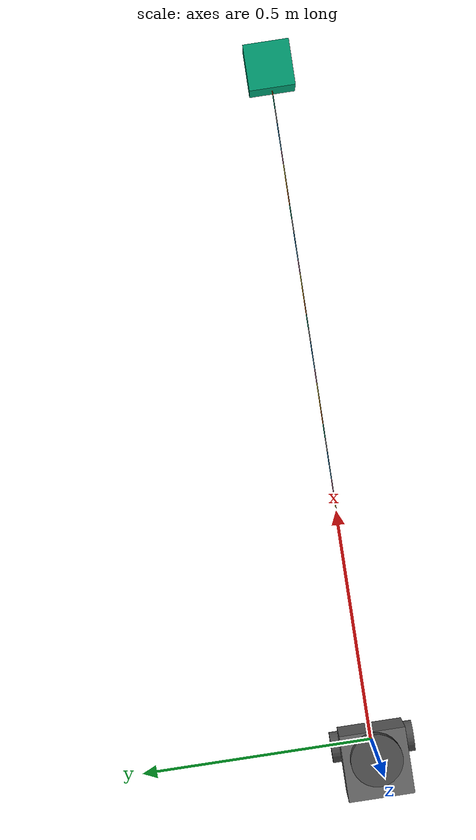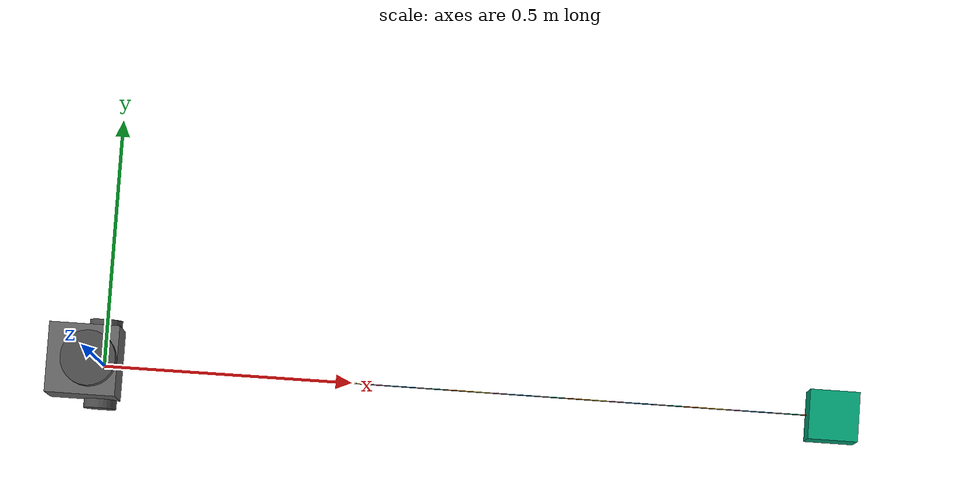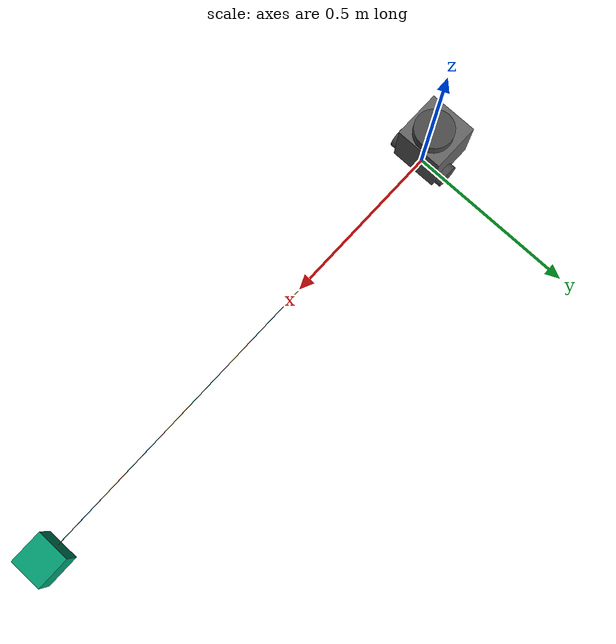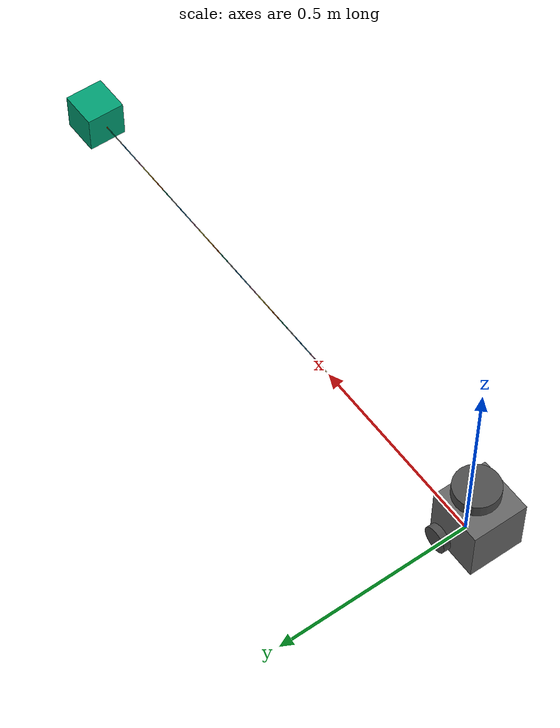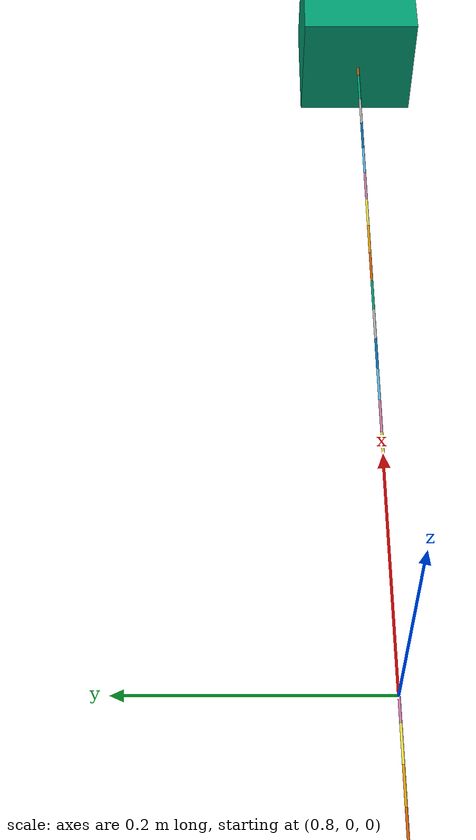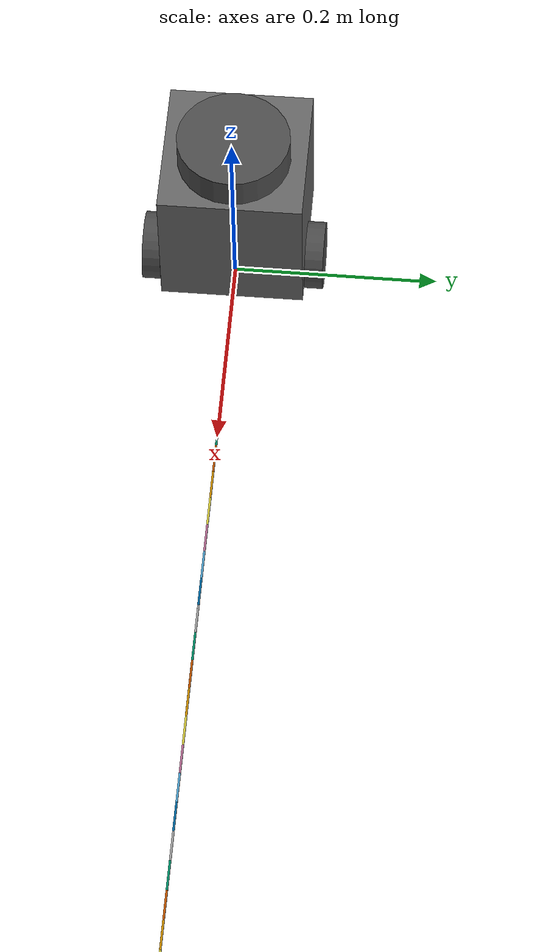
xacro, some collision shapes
<?xml version="1.0" encoding="utf-8"?>
<robot name="tether" xmlns:xacro="http://ros.org/wiki/xacro">
    <xacro:include filename="$(find world_description)/urdf/common_properties.xacro"/>
    <xacro:include filename="$(find tether_description)/urdf/tether.xacro"/>
    <xacro:include filename="$(find ugv_description)/urdf/pyramid_robotics_turtlebot3.urdf.xacro"/>

    <link name="ugv_tether_link_1">
        <inertial>
            <mass value="0.00001"/>
            <inertia ixx="0.00001" iyy="0.00001" izz="0.00001" ixy="0.00001" ixz="0.00001" iyz="0.00001"/>
        </inertial>
    </link>
    <link name="ugv_tether_link_2">
        <inertial>
            <mass value="0.00001"/>
            <inertia ixx="0.00001" iyy="0.00001" izz="0.00001" ixy="0.00001" ixz="0.00001" iyz="0.00001"/>
        </inertial>
    </link>

    <joint name="ugv_tether_joint_1" type="continuous">
        <parent link="base_footprint"/>
        <child link="ugv_tether_link_1"/>
        <axis xyz="1 0 0" />
    </joint>
    <joint name="ugv_tether_joint_2" type="continuous">
        <parent link="ugv_tether_link_1"/>
        <child link="ugv_tether_link_2"/>
        <axis xyz="0 1 0" />
    </joint>
    <joint name="ugv_tether_joint_3" type="continuous">
        <parent link="ugv_tether_link_2"/>
        <child link="tether_fragment_0"/>
        <axis xyz="0 0 1" />
        <origin xyz="0.0 0.0 0.0" rpy="0 ${pi/2} 0"/>
    </joint>

    <joint name="uav_tether_joint_4" type="fixed">
        <parent link="tether_fragment_49"/>
        <child link="pesudo_uav"/>
    </joint>

    <link name="pesudo_uav">
        <visual>
            <geometry>
                <box size="0.1 0.1 0.1"/>
            </geometry>
        </visual>
        <inertial>
            <mass value="1"/>
            <inertia ixx="1" iyy="1" izz="1" ixy="1" ixz="1" iyz="1"/>
        </inertial>
        <collision>
            <geometry>
                <box size="0.1 0.1 0.1"/>
            </geometry>
        </collision>
    </link>

    <xacro:turtlebot3_burger />
    <!--xacro:turtlebot3_burger prefix="2nd" /-->
    <xacro:tether />
</robot>

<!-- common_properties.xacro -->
<robot name="xacro_properties" xmlns:xacro="http://ros.org/wiki/xacro">

    <xacro:property name="pi" value="3.1415926535897931" />

    <!-- Init colour -->
    <material name="black">
        <color rgba="0.0 0.0 0.0 1.0"/>
    </material>

    <material name="dark">
        <color rgba="0.3 0.3 0.3 1.0"/>
    </material>
    <material name="light_black">
        <color rgba="0.4 0.4 0.4 1.0"/>
    </material>

    <material name="blue">
        <color rgba="0.0 0.0 0.8 1.0"/>
    </material>

    <material name="green">
        <color rgba="0.0 0.8 0.0 1.0"/>
    </material>

    <material name="grey">
        <color rgba="0.5 0.5 0.5 1.0"/>
    </material>

    <material name="orange">
        <color rgba="${255/255} ${108/255} ${10/255} 1.0"/>
    </material>

    <material name="brown">
        <color rgba="${222/255} ${207/255} ${195/255} 1.0"/>
    </material>

    <material name="red">
        <color rgba="0.8 0.0 0.0 1.0"/>
    </material>

    <material name="white">
        <color rgba="1.0 1.0 1.0 1.0"/>
    </material>
</robot>

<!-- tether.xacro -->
<robot xmlns:xacro="http://ros.org/wiki/xacro">
    <!--tether model-->
    <xacro:macro name="tether">
        <!--tether fragment param--><!--small link inatial--><!--link number--><!--tether_cylinder_joint--><!-- main-->
        <link name="tether_fragment_0">
            <visual>
                <origin rpy="0 0 0" xyz="0 0 0.015"/>
                <geometry>
                    <cylinder length="0.03" radius="0.001"/>
                </geometry>
                <!--material name="black"/-->
            </visual>
            <inertial>
                <mass value="0.0001"/>
                <inertia ixx="7.525e-09" iyy="7.525e-09" izz="5e-11" ixy="0.0" ixz="0.0" iyz="0.0"/>
            </inertial>
        </link>

        <link name="tether_fragment_1">
            <visual>
                <origin rpy="0 0 0" xyz="0 0 0.015"/>
                <geometry>
                    <cylinder length="0.03" radius="0.001"/>
                </geometry>
                <!--material name="black"/-->
            </visual>
            <inertial>
                <mass value="0.0001"/>
                <inertia ixx="7.525e-09" iyy="7.525e-09" izz="5e-11" ixy="0.0" ixz="0.0" iyz="0.0"/>
            </inertial>
        </link>

                <!--link between two tether fragments-->
        <link name="small_link_1_1">
            <inertial>
                <mass value="1e-05"/>
                <inertia ixx="1e-05" iyy="1e-05" izz="1e-05" ixy="0.0" ixz="0.0" iyz="0.0"/>
            </inertial>
        </link>
        <link name="small_link_2_1">
            <inertial>
                <mass value="1e-05"/>
                <inertia ixx="1e-05" iyy="1e-05" izz="1e-05" ixy="0.0" ixz="0.0" iyz="0.0"/>
            </inertial>
        </link>

        <!--tether fragment joint-->
        <joint name="joint_1_1" type="continuous">
            <origin rpy="0 0 0" xyz="0 0 0.03"/>
            <parent link="tether_fragment_0"/>
            <child link="small_link_1_1"/>
            <axis xyz="1 0 0" />
        </joint>
        <joint name="joint_2_1" type="continuous">
            <parent link="small_link_1_1"/>
            <child link="small_link_2_1"/>
            <axis xyz="0 1 0" />
        </joint>
        <joint name="joint_1_1_" type="continuous">
            <parent link="small_link_2_1"/>
            <child link="tether_fragment_1"/>
            <axis xyz="0 0 1" />
        </joint>

        <link name="tether_fragment_2">
            <visual>
                <origin rpy="0 0 0" xyz="0 0 0.015"/>
                <geometry>
                    <cylinder length="0.03" radius="0.001"/>
                </geometry>
                <!--material name="black"/-->
            </visual>
            <inertial>
                <mass value="0.0001"/>
                <inertia ixx="7.525e-09" iyy="7.525e-09" izz="5e-11" ixy="0.0" ixz="0.0" iyz="0.0"/>
            </inertial>
        </link>

                <!--link between two tether fragments-->
        <link name="small_link_1_2">
            <inertial>
                <mass value="1e-05"/>
                <inertia ixx="1e-05" iyy="1e-05" izz="1e-05" ixy="0.0" ixz="0.0" iyz="0.0"/>
            </inertial>
        </link>
        <link name="small_link_2_2">
            <inertial>
                <mass value="1e-05"/>
                <inertia ixx="1e-05" iyy="1e-05" izz="1e-05" ixy="0.0" ixz="0.0" iyz="0.0"/>
            </inertial>
        </link>

        <!--tether fragment joint-->
        <joint name="joint_1_2" type="continuous">
            <origin rpy="0 0 0" xyz="0 0 0.03"/>
            <parent link="tether_fragment_1"/>
            <child link="small_link_1_2"/>
            <axis xyz="1 0 0" />
        </joint>
        <joint name="joint_2_2" type="continuous">
            <parent link="small_link_1_2"/>
            <child link="small_link_2_2"/>
            <axis xyz="0 1 0" />
        </joint>
        <joint name="joint_1_2_" type="continuous">
            <parent link="small_link_2_2"/>
            <child link="tether_fragment_2"/>
            <axis xyz="0 0 1" />
        </joint>

        <link name="tether_fragment_3">
            <visual>
                <origin rpy="0 0 0" xyz="0 0 0.015"/>
                <geometry>
                    <cylinder length="0.03" radius="0.001"/>
                </geometry>
                <!--material name="black"/-->
            </visual>
            <inertial>
                <mass value="0.0001"/>
                <inertia ixx="7.525e-09" iyy="7.525e-09" izz="5e-11" ixy="0.0" ixz="0.0" iyz="0.0"/>
            </inertial>
        </link>

                <!--link between two tether fragments-->
        <link name="small_link_1_3">
            <inertial>
                <mass value="1e-05"/>
                <inertia ixx="1e-05" iyy="1e-05" izz="1e-05" ixy="0.0" ixz="0.0" iyz="0.0"/>
            </inertial>
        </link>
        <link name="small_link_2_3">
            <inertial>
                <mass value="1e-05"/>
                <inertia ixx="1e-05" iyy="1e-05" izz="1e-05" ixy="0.0" ixz="0.0" iyz="0.0"/>
            </inertial>
        </link>

        <!--tether fragment joint-->
        <joint name="joint_1_3" type="continuous">
            <origin rpy="0 0 0" xyz="0 0 0.03"/>
            <parent link="tether_fragment_2"/>
            <child link="small_link_1_3"/>
            <axis xyz="1 0 0" />
        </joint>
        <joint name="joint_2_3" type="continuous">
            <parent link="small_link_1_3"/>
            <child link="small_link_2_3"/>
            <axis xyz="0 1 0" />
        </joint>
        <joint name="joint_1_3_" type="continuous">
            <parent link="small_link_2_3"/>
            <child link="tether_fragment_3"/>
            <axis xyz="0 0 1" />
        </joint>

        <link name="tether_fragment_4">
            <visual>
                <origin rpy="0 0 0" xyz="0 0 0.015"/>
                <geometry>
                    <cylinder length="0.03" radius="0.001"/>
                </geometry>
                <!--material name="black"/-->
            </visual>
            <inertial>
                <mass value="0.0001"/>
                <inertia ixx="7.525e-09" iyy="7.525e-09" izz="5e-11" ixy="0.0" ixz="0.0" iyz="0.0"/>
            </inertial>
        </link>

                <!--link between two tether fragments-->
        <link name="small_link_1_4">
            <inertial>
                <mass value="1e-05"/>
                <inertia ixx="1e-05" iyy="1e-05" izz="1e-05" ixy="0.0" ixz="0.0" iyz="0.0"/>
            </inertial>
        </link>
        <link name="small_link_2_4">
            <inertial>
                <mass value="1e-05"/>
                <inertia ixx="1e-05" iyy="1e-05" izz="1e-05" ixy="0.0" ixz="0.0" iyz="0.0"/>
            </inertial>
        </link>

        <!--tether fragment joint-->
        <joint name="joint_1_4" type="continuous">
            <origin rpy="0 0 0" xyz="0 0 0.03"/>
            <parent link="tether_fragment_3"/>
            <child link="small_link_1_4"/>
            <axis xyz="1 0 0" />
        </joint>
        <joint name="joint_2_4" type="continuous">
            <parent link="small_link_1_4"/>
            <child link="small_link_2_4"/>
            <axis xyz="0 1 0" />
        </joint>
        <joint name="joint_1_4_" type="continuous">
            <parent link="small_link_2_4"/>
            <child link="tether_fragment_4"/>
            <axis xyz="0 0 1" />
        </joint>

        <link name="tether_fragment_5">
            <visual>
                <origin rpy="0 0 0" xyz="0 0 0.015"/>
                <geometry>
                    <cylinder length="0.03" radius="0.001"/>
                </geometry>
                <!--material name="black"/-->
            </visual>
            <inertial>
                <mass value="0.0001"/>
                <inertia ixx="7.525e-09" iyy="7.525e-09" izz="5e-11" ixy="0.0" ixz="0.0" iyz="0.0"/>
            </inertial>
        </link>

                <!--link between two tether fragments-->
        <link name="small_link_1_5">
            <inertial>
                <mass value="1e-05"/>
                <inertia ixx="1e-05" iyy="1e-05" izz="1e-05" ixy="0.0" ixz="0.0" iyz="0.0"/>
            </inertial>
        </link>
        <link name="small_link_2_5">
            <inertial>
                <mass value="1e-05"/>
                <inertia ixx="1e-05" iyy="1e-05" izz="1e-05" ixy="0.0" ixz="0.0" iyz="0.0"/>
            </inertial>
        </link>

        <!--tether fragment joint-->
        <joint name="joint_1_5" type="continuous">
            <origin rpy="0 0 0" xyz="0 0 0.03"/>
            <parent link="tether_fragment_4"/>
            <child link="small_link_1_5"/>
            <axis xyz="1 0 0" />
        </joint>
        <joint name="joint_2_5" type="continuous">
            <parent link="small_link_1_5"/>
            <child link="small_link_2_5"/>
            <axis xyz="0 1 0" />
        </joint>
        <joint name="joint_1_5_" type="continuous">
            <parent link="small_link_2_5"/>
            <child link="tether_fragment_5"/>
            <axis xyz="0 0 1" />
        </joint>

        <link name="tether_fragment_6">
            <visual>
                <origin rpy="0 0 0" xyz="0 0 0.015"/>
                <geometry>
                    <cylinder length="0.03" radius="0.001"/>
                </geometry>
                <!--material name="black"/-->
            </visual>
            <inertial>
                <mass value="0.0001"/>
                <inertia ixx="7.525e-09" iyy="7.525e-09" izz="5e-11" ixy="0.0" ixz="0.0" iyz="0.0"/>
            </inertial>
        </link>

                <!--link between two tether fragments-->
        <link name="small_link_1_6">
            <inertial>
                <mass value="1e-05"/>
                <inertia ixx="1e-05" iyy="1e-05" izz="1e-05" ixy="0.0" ixz="0.0" iyz="0.0"/>
            </inertial>
        </link>
        <link name="small_link_2_6">
            <inertial>
                <mass value="1e-05"/>
                <inertia ixx="1e-05" iyy="1e-05" izz="1e-05" ixy="0.0" ixz="0.0" iyz="0.0"/>
            </inertial>
        </link>

        <!--tether fragment joint-->
        <joint name="joint_1_6" type="continuous">
            <origin rpy="0 0 0" xyz="0 0 0.03"/>
            <parent link="tether_fragment_5"/>
            <child link="small_link_1_6"/>
            <axis xyz="1 0 0" />
        </joint>
        <joint name="joint_2_6" type="continuous">
            <parent link="small_link_1_6"/>
            <child link="small_link_2_6"/>
            <axis xyz="0 1 0" />
        </joint>
        <joint name="joint_1_6_" type="continuous">
            <parent link="small_link_2_6"/>
            <child link="tether_fragment_6"/>
            <axis xyz="0 0 1" />
        </joint>

        <link name="tether_fragment_7">
            <visual>
                <origin rpy="0 0 0" xyz="0 0 0.015"/>
                <geometry>
                    <cylinder length="0.03" radius="0.001"/>
                </geometry>
                <!--material name="black"/-->
            </visual>
            <inertial>
                <mass value="0.0001"/>
                <inertia ixx="7.525e-09" iyy="7.525e-09" izz="5e-11" ixy="0.0" ixz="0.0" iyz="0.0"/>
            </inertial>
        </link>

                <!--link between two tether fragments-->
        <link name="small_link_1_7">
            <inertial>
                <mass value="1e-05"/>
                <inertia ixx="1e-05" iyy="1e-05" izz="1e-05" ixy="0.0" ixz="0.0" iyz="0.0"/>
            </inertial>
        </link>
        <link name="small_link_2_7">
            <inertial>
                <mass value="1e-05"/>
                <inertia ixx="1e-05" iyy="1e-05" izz="1e-05" ixy="0.0" ixz="0.0" iyz="0.0"/>
            </inertial>
        </link>

        <!--tether fragment joint-->
        <joint name="joint_1_7" type="continuous">
            <origin rpy="0 0 0" xyz="0 0 0.03"/>
            <parent link="tether_fragment_6"/>
            <child link="small_link_1_7"/>
            <axis xyz="1 0 0" />
        </joint>
        <joint name="joint_2_7" type="continuous">
            <parent link="small_link_1_7"/>
            <child link="small_link_2_7"/>
            <axis xyz="0 1 0" />
        </joint>
        <joint name="joint_1_7_" type="continuous">
            <parent link="small_link_2_7"/>
            <child link="tether_fragment_7"/>
            <axis xyz="0 0 1" />
        </joint>

        <link name="tether_fragment_8">
            <visual>
                <origin rpy="0 0 0" xyz="0 0 0.015"/>
                <geometry>
                    <cylinder length="0.03" radius="0.001"/>
                </geometry>
                <!--material name="black"/-->
            </visual>
            <inertial>
                <mass value="0.0001"/>
                <inertia ixx="7.525e-09" iyy="7.525e-09" izz="5e-11" ixy="0.0" ixz="0.0" iyz="0.0"/>
            </inertial>
        </link>

                <!--link between two tether fragments-->
        <link name="small_link_1_8">
            <inertial>
                <mass value="1e-05"/>
                <inertia ixx="1e-05" iyy="1e-05" izz="1e-05" ixy="0.0" ixz="0.0" iyz="0.0"/>
            </inertial>
        </link>
        <link name="small_link_2_8">
            <inertial>
                <mass value="1e-05"/>
                <inertia ixx="1e-05" iyy="1e-05" izz="1e-05" ixy="0.0" ixz="0.0" iyz="0.0"/>
            </inertial>
        </link>

        <!--tether fragment joint-->
        <joint name="joint_1_8" type="continuous">
            <origin rpy="0 0 0" xyz="0 0 0.03"/>
            <parent link="tether_fragment_7"/>
            <child link="small_link_1_8"/>
            <axis xyz="1 0 0" />
        </joint>
        <joint name="joint_2_8" type="continuous">
            <parent link="small_link_1_8"/>
            <child link="small_link_2_8"/>
            <axis xyz="0 1 0" />
        </joint>
        <joint name="joint_1_8_" type="continuous">
            <parent link="small_link_2_8"/>
            <child link="tether_fragment_8"/>
            <axis xyz="0 0 1" />
        </joint>

        <link name="tether_fragment_9">
            <visual>
                <origin rpy="0 0 0" xyz="0 0 0.015"/>
                <geometry>
                    <cylinder length="0.03" radius="0.001"/>
                </geometry>
                <!--material name="black"/-->
            </visual>
            <inertial>
                <mass value="0.0001"/>
                <inertia ixx="7.525e-09" iyy="7.525e-09" izz="5e-11" ixy="0.0" ixz="0.0" iyz="0.0"/>
            </inertial>
        </link>

                <!--link between two tether fragments-->
        <link name="small_link_1_9">
            <inertial>
                <mass value="1e-05"/>
                <inertia ixx="1e-05" iyy="1e-05" izz="1e-05" ixy="0.0" ixz="0.0" iyz="0.0"/>
            </inertial>
        </link>
        <link name="small_link_2_9">
            <inertial>
                <mass value="1e-05"/>
                <inertia ixx="1e-05" iyy="1e-05" izz="1e-05" ixy="0.0" ixz="0.0" iyz="0.0"/>
            </inertial>
        </link>

        <!--tether fragment joint-->
        <joint name="joint_1_9" type="continuous">
            <origin rpy="0 0 0" xyz="0 0 0.03"/>
            <parent link="tether_fragment_8"/>
            <child link="small_link_1_9"/>
            <axis xyz="1 0 0" />
        </joint>
        <joint name="joint_2_9" type="continuous">
            <parent link="small_link_1_9"/>
            <child link="small_link_2_9"/>
            <axis xyz="0 1 0" />
        </joint>
        <joint name="joint_1_9_" type="continuous">
            <parent link="small_link_2_9"/>
            <child link="tether_fragment_9"/>
            <axis xyz="0 0 1" />
        </joint>

        <link name="tether_fragment_10">
            <visual>
                <origin rpy="0 0 0" xyz="0 0 0.015"/>
                <geometry>
                    <cylinder length="0.03" radius="0.001"/>
                </geometry>
                <!--material name="black"/-->
            </visual>
            <inertial>
                <mass value="0.0001"/>
                <inertia ixx="7.525e-09" iyy="7.525e-09" izz="5e-11" ixy="0.0" ixz="0.0" iyz="0.0"/>
            </inertial>
        </link>

                <!--link between two tether fragments-->
        <link name="small_link_1_10">
            <inertial>
                <mass value="1e-05"/>
                <inertia ixx="1e-05" iyy="1e-05" izz="1e-05" ixy="0.0" ixz="0.0" iyz="0.0"/>
            </inertial>
        </link>
        <link name="small_link_2_10">
            <inertial>
                <mass value="1e-05"/>
                <inertia ixx="1e-05" iyy="1e-05" izz="1e-05" ixy="0.0" ixz="0.0" iyz="0.0"/>
            </inertial>
        </link>

        <!--tether fragment joint-->
        <joint name="joint_1_10" type="continuous">
            <origin rpy="0 0 0" xyz="0 0 0.03"/>
            <parent link="tether_fragment_9"/>
            <child link="small_link_1_10"/>
            <axis xyz="1 0 0" />
        </joint>
        <joint name="joint_2_10" type="continuous">
            <parent link="small_link_1_10"/>
            <child link="small_link_2_10"/>
            <axis xyz="0 1 0" />
        </joint>
        <joint name="joint_1_10_" type="continuous">
            <parent link="small_link_2_10"/>
            <child link="tether_fragment_10"/>
            <axis xyz="0 0 1" />
        </joint>

        <link name="tether_fragment_11">
            <visual>
                <origin rpy="0 0 0" xyz="0 0 0.015"/>
                <geometry>
                    <cylinder length="0.03" radius="0.001"/>
                </geometry>
                <!--material name="black"/-->
            </visual>
            <inertial>
                <mass value="0.0001"/>
                <inertia ixx="7.525e-09" iyy="7.525e-09" izz="5e-11" ixy="0.0" ixz="0.0" iyz="0.0"/>
            </inertial>
        </link>

                <!--link between two tether fragments-->
        <link name="small_link_1_11">
            <inertial>
                <mass value="1e-05"/>
                <inertia ixx="1e-05" iyy="1e-05" izz="1e-05" ixy="0.0" ixz="0.0" iyz="0.0"/>
            </inertial>
        </link>
        <link name="small_link_2_11">
            <inertial>
                <mass value="1e-05"/>
                <inertia ixx="1e-05" iyy="1e-05" izz="1e-05" ixy="0.0" ixz="0.0" iyz="0.0"/>
            </inertial>
        </link>

        <!--tether fragment joint-->
        <joint name="joint_1_11" type="continuous">
            <origin rpy="0 0 0" xyz="0 0 0.03"/>
            <parent link="tether_fragment_10"/>
            <child link="small_link_1_11"/>
            <axis xyz="1 0 0" />
        </joint>
        <joint name="joint_2_11" type="continuous">
            <parent link="small_link_1_11"/>
            <child link="small_link_2_11"/>
            <axis xyz="0 1 0" />
        </joint>
        <joint name="joint_1_11_" type="continuous">
            <parent link="small_link_2_11"/>
            <child link="tether_fragment_11"/>
            <axis xyz="0 0 1" />
        </joint>

        <link name="tether_fragment_12">
            <visual>
                <origin rpy="0 0 0" xyz="0 0 0.015"/>
                <geometry>
                    <cylinder length="0.03" radius="0.001"/>
                </geometry>
                <!--material name="black"/-->
            </visual>
            <inertial>
                <mass value="0.0001"/>
                <inertia ixx="7.525e-09" iyy="7.525e-09" izz="5e-11" ixy="0.0" ixz="0.0" iyz="0.0"/>
            </inertial>
        </link>

                <!--link between two tether fragments-->
        <link name="small_link_1_12">
            <inertial>
                <mass value="1e-05"/>
                <inertia ixx="1e-05" iyy="1e-05" izz="1e-05" ixy="0.0" ixz="0.0" iyz="0.0"/>
            </inertial>
        </link>
        <link name="small_link_2_12">
            <inertial>
                <mass value="1e-05"/>
                <inertia ixx="1e-05" iyy="1e-05" izz="1e-05" ixy="0.0" ixz="0.0" iyz="0.0"/>
            </inertial>
        </link>

        <!--tether fragment joint-->
        <joint name="joint_1_12" type="continuous">
            <origin rpy="0 0 0" xyz="0 0 0.03"/>
            <parent link="tether_fragment_11"/>
            <child link="small_link_1_12"/>
            <axis xyz="1 0 0" />
        </joint>
        <joint name="joint_2_12" type="continuous">
            <parent link="small_link_1_12"/>
            <child link="small_link_2_12"/>
            <axis xyz="0 1 0" />
        </joint>
        <joint name="joint_1_12_" type="continuous">
            <parent link="small_link_2_12"/>
            <child link="tether_fragment_12"/>
            <axis xyz="0 0 1" />
        </joint>

        <link name="tether_fragment_13">
            <visual>
                <origin rpy="0 0 0" xyz="0 0 0.015"/>
                <geometry>
                    <cylinder length="0.03" radius="0.001"/>
                </geometry>
                <!--material name="black"/-->
            </visual>
            <inertial>
                <mass value="0.0001"/>
                <inertia ixx="7.525e-09" iyy="7.525e-09" izz="5e-11" ixy="0.0" ixz="0.0" iyz="0.0"/>
            </inertial>
        </link>

                <!--link between two tether fragments-->
        <link name="small_link_1_13">
            <inertial>
                <mass value="1e-05"/>
                <inertia ixx="1e-05" iyy="1e-05" izz="1e-05" ixy="0.0" ixz="0.0" iyz="0.0"/>
            </inertial>
        </link>
        <link name="small_link_2_13">
            <inertial>
                <mass value="1e-05"/>
                <inertia ixx="1e-05" iyy="1e-05" izz="1e-05" ixy="0.0" ixz="0.0" iyz="0.0"/>
            </inertial>
        </link>

        <!--tether fragment joint-->
        <joint name="joint_1_13" type="continuous">
            <origin rpy="0 0 0" xyz="0 0 0.03"/>
            <parent link="tether_fragment_12"/>
            <child link="small_link_1_13"/>
            <axis xyz="1 0 0" />
        </joint>
        <joint name="joint_2_13" type="continuous">
            <parent link="small_link_1_13"/>
            <child link="small_link_2_13"/>
            <axis xyz="0 1 0" />
        </joint>
        <joint name="joint_1_13_" type="continuous">
            <parent link="small_link_2_13"/>
            <child link="tether_fragment_13"/>
            <axis xyz="0 0 1" />
        </joint>

        <link name="tether_fragment_14">
            <visual>
                <origin rpy="0 0 0" xyz="0 0 0.015"/>
                <geometry>
                    <cylinder length="0.03" radius="0.001"/>
                </geometry>
                <!--material name="black"/-->
            </visual>
            <inertial>
                <mass value="0.0001"/>
                <inertia ixx="7.525e-09" iyy="7.525e-09" izz="5e-11" ixy="0.0" ixz="0.0" iyz="0.0"/>
            </inertial>
        </link>

                <!--link between two tether fragments-->
        <link name="small_link_1_14">
            <inertial>
                <mass value="1e-05"/>
                <inertia ixx="1e-05" iyy="1e-05" izz="1e-05" ixy="0.0" ixz="0.0" iyz="0.0"/>
            </inertial>
        </link>
        <link name="small_link_2_14">
            <inertial>
                <mass value="1e-05"/>
                <inertia ixx="1e-05" iyy="1e-05" izz="1e-05" ixy="0.0" ixz="0.0" iyz="0.0"/>
            </inertial>
        </link>

        <!--tether fragment joint-->
        <joint name="joint_1_14" type="continuous">
            <origin rpy="0 0 0" xyz="0 0 0.03"/>
            <parent link="tether_fragment_13"/>
            <child link="small_link_1_14"/>
            <axis xyz="1 0 0" />
        </joint>
        <joint name="joint_2_14" type="continuous">
            <parent link="small_link_1_14"/>
            <child link="small_link_2_14"/>
            <axis xyz="0 1 0" />
        </joint>
        <joint name="joint_1_14_" type="continuous">
            <parent link="small_link_2_14"/>
            <child link="tether_fragment_14"/>
            <axis xyz="0 0 1" />
        </joint>

        <link name="tether_fragment_15">
            <visual>
                <origin rpy="0 0 0" xyz="0 0 0.015"/>
                <geometry>
                    <cylinder length="0.03" radius="0.001"/>
                </geometry>
                <!--material name="black"/-->
            </visual>
            <inertial>
                <mass value="0.0001"/>
                <inertia ixx="7.525e-09" iyy="7.525e-09" izz="5e-11" ixy="0.0" ixz="0.0" iyz="0.0"/>
            </inertial>
        </link>

                <!--link between two tether fragments-->
        <link name="small_link_1_15">
            <inertial>
                <mass value="1e-05"/>
                <inertia ixx="1e-05" iyy="1e-05" izz="1e-05" ixy="0.0" ixz="0.0" iyz="0.0"/>
            </inertial>
        </link>
        <link name="small_link_2_15">
            <inertial>
                <mass value="1e-05"/>
                <inertia ixx="1e-05" iyy="1e-05" izz="1e-05" ixy="0.0" ixz="0.0" iyz="0.0"/>
            </inertial>
        </link>

        <!--tether fragment joint-->
        <joint name="joint_1_15" type="continuous">
            <origin rpy="0 0 0" xyz="0 0 0.03"/>
            <parent link="tether_fragment_14"/>
            <child link="small_link_1_15"/>
            <axis xyz="1 0 0" />
        </joint>
        <joint name="joint_2_15" type="continuous">
            <parent link="small_link_1_15"/>
            <child link="small_link_2_15"/>
            <axis xyz="0 1 0" />
        </joint>
        <joint name="joint_1_15_" type="continuous">
            <parent link="small_link_2_15"/>
            <child link="tether_fragment_15"/>
            <axis xyz="0 0 1" />
        </joint>

        <link name="tether_fragment_16">
            <visual>
                <origin rpy="0 0 0" xyz="0 0 0.015"/>
                <geometry>
                    <cylinder length="0.03" radius="0.001"/>
                </geometry>
                <!--material name="black"/-->
            </visual>
            <inertial>
                <mass value="0.0001"/>
                <inertia ixx="7.525e-09" iyy="7.525e-09" izz="5e-11" ixy="0.0" ixz="0.0" iyz="0.0"/>
            </inertial>
        </link>

                <!--link between two tether fragments-->
        <link name="small_link_1_16">
            <inertial>
                <mass value="1e-05"/>
                <inertia ixx="1e-05" iyy="1e-05" izz="1e-05" ixy="0.0" ixz="0.0" iyz="0.0"/>
            </inertial>
        </link>
        <link name="small_link_2_16">
            <inertial>
                <mass value="1e-05"/>
                <inertia ixx="1e-05" iyy="1e-05" izz="1e-05" ixy="0.0" ixz="0.0" iyz="0.0"/>
            </inertial>
        </link>

        <!--tether fragment joint-->
        <joint name="joint_1_16" type="continuous">
            <origin rpy="0 0 0" xyz="0 0 0.03"/>
            <parent link="tether_fragment_15"/>
            <child link="small_link_1_16"/>
            <axis xyz="1 0 0" />
        </joint>
        <joint name="joint_2_16" type="continuous">
            <parent link="small_link_1_16"/>
            <child link="small_link_2_16"/>
            <axis xyz="0 1 0" />
        </joint>
        <joint name="joint_1_16_" type="continuous">
            <parent link="small_link_2_16"/>
            <child link="tether_fragment_16"/>
            <axis xyz="0 0 1" />
        </joint>

        <link name="tether_fragment_17">
            <visual>
                <origin rpy="0 0 0" xyz="0 0 0.015"/>
                <geometry>
                    <cylinder length="0.03" radius="0.001"/>
                </geometry>
                <!--material name="black"/-->
            </visual>
            <inertial>
                <mass value="0.0001"/>
                <inertia ixx="7.525e-09" iyy="7.525e-09" izz="5e-11" ixy="0.0" ixz="0.0" iyz="0.0"/>
            </inertial>
        </link>

                <!--link between two tether fragments-->
        <link name="small_link_1_17">
            <inertial>
                <mass value="1e-05"/>
                <inertia ixx="1e-05" iyy="1e-05" izz="1e-05" ixy="0.0" ixz="0.0" iyz="0.0"/>
            </inertial>
        </link>
        <link name="small_link_2_17">
            <inertial>
                <mass value="1e-05"/>
                <inertia ixx="1e-05" iyy="1e-05" izz="1e-05" ixy="0.0" ixz="0.0" iyz="0.0"/>
            </inertial>
        </link>

        <!--tether fragment joint-->
        <joint name="joint_1_17" type="continuous">
            <origin rpy="0 0 0" xyz="0 0 0.03"/>
            <parent link="tether_fragment_16"/>
            <child link="small_link_1_17"/>
            <axis xyz="1 0 0" />
        </joint>
        <joint name="joint_2_17" type="continuous">
            <parent link="small_link_1_17"/>
            <child link="small_link_2_17"/>
            <axis xyz="0 1 0" />
        </joint>
        <joint name="joint_1_17_" type="continuous">
            <parent link="small_link_2_17"/>
            <child link="tether_fragment_17"/>
            <axis xyz="0 0 1" />
        </joint>

        <link name="tether_fragment_18">
            <visual>
                <origin rpy="0 0 0" xyz="0 0 0.015"/>
                <geometry>
                    <cylinder length="0.03" radius="0.001"/>
                </geometry>
                <!--material name="black"/-->
            </visual>
            <inertial>
                <mass value="0.0001"/>
                <inertia ixx="7.525e-09" iyy="7.525e-09" izz="5e-11" ixy="0.0" ixz="0.0" iyz="0.0"/>
            </inertial>
        </link>

                <!--link between two tether fragments-->
        <link name="small_link_1_18">
            <inertial>
                <mass value="1e-05"/>
                <inertia ixx="1e-05" iyy="1e-05" izz="1e-05" ixy="0.0" ixz="0.0" iyz="0.0"/>
            </inertial>
        </link>
        <link name="small_link_2_18">
            <inertial>
                <mass value="1e-05"/>
                <inertia ixx="1e-05" iyy="1e-05" izz="1e-05" ixy="0.0" ixz="0.0" iyz="0.0"/>
            </inertial>
        </link>

        <!--tether fragment joint-->
        <joint name="joint_1_18" type="continuous">
            <origin rpy="0 0 0" xyz="0 0 0.03"/>
            <parent link="tether_fragment_17"/>
            <child link="small_link_1_18"/>
            <axis xyz="1 0 0" />
        </joint>
        <joint name="joint_2_18" type="continuous">
            <parent link="small_link_1_18"/>
            <child link="small_link_2_18"/>
            <axis xyz="0 1 0" />
        </joint>
        <joint name="joint_1_18_" type="continuous">
            <parent link="small_link_2_18"/>
            <child link="tether_fragment_18"/>
            <axis xyz="0 0 1" />
        </joint>

        <link name="tether_fragment_19">
            <visual>
                <origin rpy="0 0 0" xyz="0 0 0.015"/>
                <geometry>
                    <cylinder length="0.03" radius="0.001"/>
                </geometry>
                <!--material name="black"/-->
            </visual>
            <inertial>
                <mass value="0.0001"/>
                <inertia ixx="7.525e-09" iyy="7.525e-09" izz="5e-11" ixy="0.0" ixz="0.0" iyz="0.0"/>
            </inertial>
        </link>

                <!--link between two tether fragments-->
        <link name="small_link_1_19">
            <inertial>
                <mass value="1e-05"/>
                <inertia ixx="1e-05" iyy="1e-05" izz="1e-05" ixy="0.0" ixz="0.0" iyz="0.0"/>
            </inertial>
        </link>
        <link name="small_link_2_19">
            <inertial>
                <mass value="1e-05"/>
                <inertia ixx="1e-05" iyy="1e-05" izz="1e-05" ixy="0.0" ixz="0.0" iyz="0.0"/>
            </inertial>
        </link>

        <!--tether fragment joint-->
        <joint name="joint_1_19" type="continuous">
            <origin rpy="0 0 0" xyz="0 0 0.03"/>
            <parent link="tether_fragment_18"/>
            <child link="small_link_1_19"/>
            <axis xyz="1 0 0" />
        </joint>
        <joint name="joint_2_19" type="continuous">
            <parent link="small_link_1_19"/>
            <child link="small_link_2_19"/>
            <axis xyz="0 1 0" />
        </joint>
        <joint name="joint_1_19_" type="continuous">
            <parent link="small_link_2_19"/>
            <child link="tether_fragment_19"/>
            <axis xyz="0 0 1" />
        </joint>

        <link name="tether_fragment_20">
            <visual>
                <origin rpy="0 0 0" xyz="0 0 0.015"/>
                <geometry>
                    <cylinder length="0.03" radius="0.001"/>
                </geometry>
                <!--material name="black"/-->
            </visual>
            <inertial>
                <mass value="0.0001"/>
                <inertia ixx="7.525e-09" iyy="7.525e-09" izz="5e-11" ixy="0.0" ixz="0.0" iyz="0.0"/>
            </inertial>
        </link>

                <!--link between two tether fragments-->
        <link name="small_link_1_20">
            <inertial>
                <mass value="1e-05"/>
                <inertia ixx="1e-05" iyy="1e-05" izz="1e-05" ixy="0.0" ixz="0.0" iyz="0.0"/>
            </inertial>
        </link>
        <link name="small_link_2_20">
            <inertial>
                <mass value="1e-05"/>
                <inertia ixx="1e-05" iyy="1e-05" izz="1e-05" ixy="0.0" ixz="0.0" iyz="0.0"/>
            </inertial>
        </link>

        <!--tether fragment joint-->
        <joint name="joint_1_20" type="continuous">
            <origin rpy="0 0 0" xyz="0 0 0.03"/>
            <parent link="tether_fragment_19"/>
            <child link="small_link_1_20"/>
            <axis xyz="1 0 0" />
        </joint>
        <joint name="joint_2_20" type="continuous">
            <parent link="small_link_1_20"/>
            <child link="small_link_2_20"/>
            <axis xyz="0 1 0" />
        </joint>
        <joint name="joint_1_20_" type="continuous">
            <parent link="small_link_2_20"/>
            <child link="tether_fragment_20"/>
            <axis xyz="0 0 1" />
        </joint>

        <link name="tether_fragment_21">
            <visual>
                <origin rpy="0 0 0" xyz="0 0 0.015"/>
                <geometry>
                    <cylinder length="0.03" radius="0.001"/>
                </geometry>
                <!--material name="black"/-->
            </visual>
            <inertial>
                <mass value="0.0001"/>
                <inertia ixx="7.525e-09" iyy="7.525e-09" izz="5e-11" ixy="0.0" ixz="0.0" iyz="0.0"/>
            </inertial>
        </link>

                <!--link between two tether fragments-->
        <link name="small_link_1_21">
            <inertial>
                <mass value="1e-05"/>
                <inertia ixx="1e-05" iyy="1e-05" izz="1e-05" ixy="0.0" ixz="0.0" iyz="0.0"/>
            </inertial>
        </link>
        <link name="small_link_2_21">
            <inertial>
                <mass value="1e-05"/>
                <inertia ixx="1e-05" iyy="1e-05" izz="1e-05" ixy="0.0" ixz="0.0" iyz="0.0"/>
            </inertial>
        </link>

        <!--tether fragment joint-->
        <joint name="joint_1_21" type="continuous">
            <origin rpy="0 0 0" xyz="0 0 0.03"/>
            <parent link="tether_fragment_20"/>
            <child link="small_link_1_21"/>
            <axis xyz="1 0 0" />
        </joint>
        <joint name="joint_2_21" type="continuous">
            <parent link="small_link_1_21"/>
            <child link="small_link_2_21"/>
            <axis xyz="0 1 0" />
        </joint>
        <joint name="joint_1_21_" type="continuous">
            <parent link="small_link_2_21"/>
            <child link="tether_fragment_21"/>
            <axis xyz="0 0 1" />
        </joint>

        <link name="tether_fragment_22">
            <visual>
                <origin rpy="0 0 0" xyz="0 0 0.015"/>
                <geometry>
                    <cylinder length="0.03" radius="0.001"/>
                </geometry>
                <!--material name="black"/-->
            </visual>
            <inertial>
                <mass value="0.0001"/>
                <inertia ixx="7.525e-09" iyy="7.525e-09" izz="5e-11" ixy="0.0" ixz="0.0" iyz="0.0"/>
            </inertial>
        </link>

                <!--link between two tether fragments-->
        <link name="small_link_1_22">
            <inertial>
                <mass value="1e-05"/>
                <inertia ixx="1e-05" iyy="1e-05" izz="1e-05" ixy="0.0" ixz="0.0" iyz="0.0"/>
            </inertial>
        </link>
        <link name="small_link_2_22">
            <inertial>
                <mass value="1e-05"/>
                <inertia ixx="1e-05" iyy="1e-05" izz="1e-05" ixy="0.0" ixz="0.0" iyz="0.0"/>
            </inertial>
        </link>

        <!--tether fragment joint-->
        <joint name="joint_1_22" type="continuous">
            <origin rpy="0 0 0" xyz="0 0 0.03"/>
            <parent link="tether_fragment_21"/>
            <child link="small_link_1_22"/>
            <axis xyz="1 0 0" />
        </joint>
        <joint name="joint_2_22" type="continuous">
            <parent link="small_link_1_22"/>
            <child link="small_link_2_22"/>
            <axis xyz="0 1 0" />
        </joint>
        <joint name="joint_1_22_" type="continuous">
            <parent link="small_link_2_22"/>
            <child link="tether_fragment_22"/>
            <axis xyz="0 0 1" />
        </joint>

        <link name="tether_fragment_23">
            <visual>
                <origin rpy="0 0 0" xyz="0 0 0.015"/>
                <geometry>
                    <cylinder length="0.03" radius="0.001"/>
                </geometry>
                <!--material name="black"/-->
            </visual>
            <inertial>
                <mass value="0.0001"/>
                <inertia ixx="7.525e-09" iyy="7.525e-09" izz="5e-11" ixy="0.0" ixz="0.0" iyz="0.0"/>
            </inertial>
        </link>

                <!--link between two tether fragments-->
        <link name="small_link_1_23">
            <inertial>
                <mass value="1e-05"/>
                <inertia ixx="1e-05" iyy="1e-05" izz="1e-05" ixy="0.0" ixz="0.0" iyz="0.0"/>
            </inertial>
        </link>
        <link name="small_link_2_23">
            <inertial>
                <mass value="1e-05"/>
                <inertia ixx="1e-05" iyy="1e-05" izz="1e-05" ixy="0.0" ixz="0.0" iyz="0.0"/>
            </inertial>
        </link>

        <!--tether fragment joint-->
        <joint name="joint_1_23" type="continuous">
            <origin rpy="0 0 0" xyz="0 0 0.03"/>
            <parent link="tether_fragment_22"/>
            <child link="small_link_1_23"/>
            <axis xyz="1 0 0" />
        </joint>
        <joint name="joint_2_23" type="continuous">
            <parent link="small_link_1_23"/>
            <child link="small_link_2_23"/>
            <axis xyz="0 1 0" />
        </joint>
        <joint name="joint_1_23_" type="continuous">
            <parent link="small_link_2_23"/>
            <child link="tether_fragment_23"/>
            <axis xyz="0 0 1" />
        </joint>

        <link name="tether_fragment_24">
            <visual>
                <origin rpy="0 0 0" xyz="0 0 0.015"/>
                <geometry>
                    <cylinder length="0.03" radius="0.001"/>
                </geometry>
                <!--material name="black"/-->
            </visual>
            <inertial>
                <mass value="0.0001"/>
                <inertia ixx="7.525e-09" iyy="7.525e-09" izz="5e-11" ixy="0.0" ixz="0.0" iyz="0.0"/>
            </inertial>
        </link>

                <!--link between two tether fragments-->
        <link name="small_link_1_24">
            <inertial>
                <mass value="1e-05"/>
                <inertia ixx="1e-05" iyy="1e-05" izz="1e-05" ixy="0.0" ixz="0.0" iyz="0.0"/>
            </inertial>
        </link>
        <link name="small_link_2_24">
            <inertial>
                <mass value="1e-05"/>
                <inertia ixx="1e-05" iyy="1e-05" izz="1e-05" ixy="0.0" ixz="0.0" iyz="0.0"/>
            </inertial>
        </link>

        <!--tether fragment joint-->
        <joint name="joint_1_24" type="continuous">
            <origin rpy="0 0 0" xyz="0 0 0.03"/>
            <parent link="tether_fragment_23"/>
            <child link="small_link_1_24"/>
            <axis xyz="1 0 0" />
        </joint>
        <joint name="joint_2_24" type="continuous">
            <parent link="small_link_1_24"/>
            <child link="small_link_2_24"/>
            <axis xyz="0 1 0" />
        </joint>
        <joint name="joint_1_24_" type="continuous">
            <parent link="small_link_2_24"/>
            <child link="tether_fragment_24"/>
            <axis xyz="0 0 1" />
        </joint>

        <link name="tether_fragment_25">
            <visual>
                <origin rpy="0 0 0" xyz="0 0 0.015"/>
                <geometry>
                    <cylinder length="0.03" radius="0.001"/>
                </geometry>
                <!--material name="black"/-->
            </visual>
            <inertial>
                <mass value="0.0001"/>
                <inertia ixx="7.525e-09" iyy="7.525e-09" izz="5e-11" ixy="0.0" ixz="0.0" iyz="0.0"/>
            </inertial>
        </link>

                <!--link between two tether fragments-->
        <link name="small_link_1_25">
            <inertial>
                <mass value="1e-05"/>
                <inertia ixx="1e-05" iyy="1e-05" izz="1e-05" ixy="0.0" ixz="0.0" iyz="0.0"/>
            </inertial>
        </link>
        <link name="small_link_2_25">
            <inertial>
                <mass value="1e-05"/>
                <inertia ixx="1e-05" iyy="1e-05" izz="1e-05" ixy="0.0" ixz="0.0" iyz="0.0"/>
            </inertial>
        </link>

        <!--tether fragment joint-->
        <joint name="joint_1_25" type="continuous">
            <origin rpy="0 0 0" xyz="0 0 0.03"/>
            <parent link="tether_fragment_24"/>
            <child link="small_link_1_25"/>
            <axis xyz="1 0 0" />
        </joint>
        <joint name="joint_2_25" type="continuous">
            <parent link="small_link_1_25"/>
            <child link="small_link_2_25"/>
            <axis xyz="0 1 0" />
        </joint>
        <joint name="joint_1_25_" type="continuous">
            <parent link="small_link_2_25"/>
            <child link="tether_fragment_25"/>
            <axis xyz="0 0 1" />
        </joint>

        <link name="tether_fragment_26">
            <visual>
                <origin rpy="0 0 0" xyz="0 0 0.015"/>
                <geometry>
                    <cylinder length="0.03" radius="0.001"/>
                </geometry>
                <!--material name="black"/-->
            </visual>
            <inertial>
                <mass value="0.0001"/>
                <inertia ixx="7.525e-09" iyy="7.525e-09" izz="5e-11" ixy="0.0" ixz="0.0" iyz="0.0"/>
            </inertial>
        </link>

                <!--link between two tether fragments-->
        <link name="small_link_1_26">
            <inertial>
                <mass value="1e-05"/>
                <inertia ixx="1e-05" iyy="1e-05" izz="1e-05" ixy="0.0" ixz="0.0" iyz="0.0"/>
            </inertial>
        </link>
        <link name="small_link_2_26">
            <inertial>
                <mass value="1e-05"/>
                <inertia ixx="1e-05" iyy="1e-05" izz="1e-05" ixy="0.0" ixz="0.0" iyz="0.0"/>
            </inertial>
        </link>

        <!--tether fragment joint-->
        <joint name="joint_1_26" type="continuous">
            <origin rpy="0 0 0" xyz="0 0 0.03"/>
            <parent link="tether_fragment_25"/>
            <child link="small_link_1_26"/>
            <axis xyz="1 0 0" />
        </joint>
        <joint name="joint_2_26" type="continuous">
            <parent link="small_link_1_26"/>
            <child link="small_link_2_26"/>
            <axis xyz="0 1 0" />
        </joint>
        <joint name="joint_1_26_" type="continuous">
            <parent link="small_link_2_26"/>
            <child link="tether_fragment_26"/>
            <axis xyz="0 0 1" />
        </joint>

        <link name="tether_fragment_27">
            <visual>
                <origin rpy="0 0 0" xyz="0 0 0.015"/>
                <geometry>
                    <cylinder length="0.03" radius="0.001"/>
                </geometry>
                <!--material name="black"/-->
            </visual>
            <inertial>
                <mass value="0.0001"/>
                <inertia ixx="7.525e-09" iyy="7.525e-09" izz="5e-11" ixy="0.0" ixz="0.0" iyz="0.0"/>
            </inertial>
        </link>

                <!--link between two tether fragments-->
        <link name="small_link_1_27">
            <inertial>
                <mass value="1e-05"/>
                <inertia ixx="1e-05" iyy="1e-05" izz="1e-05" ixy="0.0" ixz="0.0" iyz="0.0"/>
            </inertial>
        </link>
        <link name="small_link_2_27">
            <inertial>
                <mass value="1e-05"/>
                <inertia ixx="1e-05" iyy="1e-05" izz="1e-05" ixy="0.0" ixz="0.0" iyz="0.0"/>
            </inertial>
        </link>

        <!--tether fragment joint-->
        <joint name="joint_1_27" type="continuous">
            <origin rpy="0 0 0" xyz="0 0 0.03"/>
            <parent link="tether_fragment_26"/>
            <child link="small_link_1_27"/>
            <axis xyz="1 0 0" />
        </joint>
        <joint name="joint_2_27" type="continuous">
            <parent link="small_link_1_27"/>
            <child link="small_link_2_27"/>
            <axis xyz="0 1 0" />
        </joint>
        <joint name="joint_1_27_" type="continuous">
            <parent link="small_link_2_27"/>
            <child link="tether_fragment_27"/>
            <axis xyz="0 0 1" />
        </joint>

        <link name="tether_fragment_28">
            <visual>
                <origin rpy="0 0 0" xyz="0 0 0.015"/>
                <geometry>
                    <cylinder length="0.03" radius="0.001"/>
                </geometry>
                <!--material name="black"/-->
            </visual>
            <inertial>
                <mass value="0.0001"/>
                <inertia ixx="7.525e-09" iyy="7.525e-09" izz="5e-11" ixy="0.0" ixz="0.0" iyz="0.0"/>
            </inertial>
        </link>

                <!--link between two tether fragments-->
        <link name="small_link_1_28">
            <inertial>
                <mass value="1e-05"/>
                <inertia ixx="1e-05" iyy="1e-05" izz="1e-05" ixy="0.0" ixz="0.0" iyz="0.0"/>
            </inertial>
        </link>
        <link name="small_link_2_28">
            <inertial>
                <mass value="1e-05"/>
                <inertia ixx="1e-05" iyy="1e-05" izz="1e-05" ixy="0.0" ixz="0.0" iyz="0.0"/>
            </inertial>
        </link>

        <!--tether fragment joint-->
        <joint name="joint_1_28" type="continuous">
            <origin rpy="0 0 0" xyz="0 0 0.03"/>
            <parent link="tether_fragment_27"/>
            <child link="small_link_1_28"/>
            <axis xyz="1 0 0" />
        </joint>
        <joint name="joint_2_28" type="continuous">
            <parent link="small_link_1_28"/>
            <child link="small_link_2_28"/>
            <axis xyz="0 1 0" />
        </joint>
        <joint name="joint_1_28_" type="continuous">
            <parent link="small_link_2_28"/>
            <child link="tether_fragment_28"/>
            <axis xyz="0 0 1" />
        </joint>

        <link name="tether_fragment_29">
            <visual>
                <origin rpy="0 0 0" xyz="0 0 0.015"/>
                <geometry>
                    <cylinder length="0.03" radius="0.001"/>
                </geometry>
                <!--material name="black"/-->
            </visual>
            <inertial>
                <mass value="0.0001"/>
                <inertia ixx="7.525e-09" iyy="7.525e-09" izz="5e-11" ixy="0.0" ixz="0.0" iyz="0.0"/>
            </inertial>
        </link>

                <!--link between two tether fragments-->
        <link name="small_link_1_29">
            <inertial>
                <mass value="1e-05"/>
                <inertia ixx="1e-05" iyy="1e-05" izz="1e-05" ixy="0.0" ixz="0.0" iyz="0.0"/>
            </inertial>
        </link>
        <link name="small_link_2_29">
            <inertial>
                <mass value="1e-05"/>
                <inertia ixx="1e-05" iyy="1e-05" izz="1e-05" ixy="0.0" ixz="0.0" iyz="0.0"/>
            </inertial>
        </link>

        <!--tether fragment joint-->
        <joint name="joint_1_29" type="continuous">
            <origin rpy="0 0 0" xyz="0 0 0.03"/>
            <parent link="tether_fragment_28"/>
            <child link="small_link_1_29"/>
            <axis xyz="1 0 0" />
        </joint>
        <joint name="joint_2_29" type="continuous">
            <parent link="small_link_1_29"/>
            <child link="small_link_2_29"/>
            <axis xyz="0 1 0" />
        </joint>
        <joint name="joint_1_29_" type="continuous">
            <parent link="small_link_2_29"/>
            <child link="tether_fragment_29"/>
            <axis xyz="0 0 1" />
        </joint>

        <link name="tether_fragment_30">
            <visual>
                <origin rpy="0 0 0" xyz="0 0 0.015"/>
                <geometry>
                    <cylinder length="0.03" radius="0.001"/>
                </geometry>
                <!--material name="black"/-->
            </visual>
            <inertial>
                <mass value="0.0001"/>
                <inertia ixx="7.525e-09" iyy="7.525e-09" izz="5e-11" ixy="0.0" ixz="0.0" iyz="0.0"/>
            </inertial>
        </link>

                <!--link between two tether fragments-->
        <link name="small_link_1_30">
            <inertial>
                <mass value="1e-05"/>
                <inertia ixx="1e-05" iyy="1e-05" izz="1e-05" ixy="0.0" ixz="0.0" iyz="0.0"/>
            </inertial>
        </link>
        <link name="small_link_2_30">
            <inertial>
                <mass value="1e-05"/>
                <inertia ixx="1e-05" iyy="1e-05" izz="1e-05" ixy="0.0" ixz="0.0" iyz="0.0"/>
            </inertial>
        </link>

        <!--tether fragment joint-->
        <joint name="joint_1_30" type="continuous">
            <origin rpy="0 0 0" xyz="0 0 0.03"/>
            <parent link="tether_fragment_29"/>
            <child link="small_link_1_30"/>
            <axis xyz="1 0 0" />
        </joint>
        <joint name="joint_2_30" type="continuous">
            <parent link="small_link_1_30"/>
            <child link="small_link_2_30"/>
            <axis xyz="0 1 0" />
        </joint>
        <joint name="joint_1_30_" type="continuous">
            <parent link="small_link_2_30"/>
            <child link="tether_fragment_30"/>
            <axis xyz="0 0 1" />
        </joint>

        <link name="tether_fragment_31">
            <visual>
                <origin rpy="0 0 0" xyz="0 0 0.015"/>
                <geometry>
                    <cylinder length="0.03" radius="0.001"/>
                </geometry>
                <!--material name="black"/-->
            </visual>
            <inertial>
                <mass value="0.0001"/>
                <inertia ixx="7.525e-09" iyy="7.525e-09" izz="5e-11" ixy="0.0" ixz="0.0" iyz="0.0"/>
            </inertial>
        </link>

                <!--link between two tether fragments-->
        <link name="small_link_1_31">
            <inertial>
                <mass value="1e-05"/>
                <inertia ixx="1e-05" iyy="1e-05" izz="1e-05" ixy="0.0" ixz="0.0" iyz="0.0"/>
            </inertial>
        </link>
        <link name="small_link_2_31">
            <inertial>
                <mass value="1e-05"/>
                <inertia ixx="1e-05" iyy="1e-05" izz="1e-05" ixy="0.0" ixz="0.0" iyz="0.0"/>
            </inertial>
        </link>

        <!--tether fragment joint-->
        <joint name="joint_1_31" type="continuous">
            <origin rpy="0 0 0" xyz="0 0 0.03"/>
            <parent link="tether_fragment_30"/>
            <child link="small_link_1_31"/>
            <axis xyz="1 0 0" />
        </joint>
        <joint name="joint_2_31" type="continuous">
            <parent link="small_link_1_31"/>
            <child link="small_link_2_31"/>
            <axis xyz="0 1 0" />
        </joint>
        <joint name="joint_1_31_" type="continuous">
            <parent link="small_link_2_31"/>
            <child link="tether_fragment_31"/>
            <axis xyz="0 0 1" />
        </joint>

        <link name="tether_fragment_32">
            <visual>
                <origin rpy="0 0 0" xyz="0 0 0.015"/>
                <geometry>
                    <cylinder length="0.03" radius="0.001"/>
                </geometry>
                <!--material name="black"/-->
            </visual>
            <inertial>
                <mass value="0.0001"/>
                <inertia ixx="7.525e-09" iyy="7.525e-09" izz="5e-11" ixy="0.0" ixz="0.0" iyz="0.0"/>
            </inertial>
        </link>

                <!--link between two tether fragments-->
        <link name="small_link_1_32">
            <inertial>
                <mass value="1e-05"/>
                <inertia ixx="1e-05" iyy="1e-05" izz="1e-05" ixy="0.0" ixz="0.0" iyz="0.0"/>
            </inertial>
        </link>
        <link name="small_link_2_32">
            <inertial>
                <mass value="1e-05"/>
                <inertia ixx="1e-05" iyy="1e-05" izz="1e-05" ixy="0.0" ixz="0.0" iyz="0.0"/>
            </inertial>
        </link>

        <!--tether fragment joint-->
        <joint name="joint_1_32" type="continuous">
            <origin rpy="0 0 0" xyz="0 0 0.03"/>
            <parent link="tether_fragment_31"/>
            <child link="small_link_1_32"/>
            <axis xyz="1 0 0" />
        </joint>
        <joint name="joint_2_32" type="continuous">
            <parent link="small_link_1_32"/>
            <child link="small_link_2_32"/>
            <axis xyz="0 1 0" />
        </joint>
        <joint name="joint_1_32_" type="continuous">
            <parent link="small_link_2_32"/>
            <child link="tether_fragment_32"/>
            <axis xyz="0 0 1" />
        </joint>

        <link name="tether_fragment_33">
            <visual>
                <origin rpy="0 0 0" xyz="0 0 0.015"/>
                <geometry>
                    <cylinder length="0.03" radius="0.001"/>
                </geometry>
                <!--material name="black"/-->
            </visual>
            <inertial>
                <mass value="0.0001"/>
                <inertia ixx="7.525e-09" iyy="7.525e-09" izz="5e-11" ixy="0.0" ixz="0.0" iyz="0.0"/>
            </inertial>
        </link>

                <!--link between two tether fragments-->
        <link name="small_link_1_33">
            <inertial>
                <mass value="1e-05"/>
                <inertia ixx="1e-05" iyy="1e-05" izz="1e-05" ixy="0.0" ixz="0.0" iyz="0.0"/>
            </inertial>
        </link>
        <link name="small_link_2_33">
            <inertial>
                <mass value="1e-05"/>
                <inertia ixx="1e-05" iyy="1e-05" izz="1e-05" ixy="0.0" ixz="0.0" iyz="0.0"/>
            </inertial>
        </link>

        <!--tether fragment joint-->
        <joint name="joint_1_33" type="continuous">
            <origin rpy="0 0 0" xyz="0 0 0.03"/>
            <parent link="tether_fragment_32"/>
            <child link="small_link_1_33"/>
            <axis xyz="1 0 0" />
        </joint>
        <joint name="joint_2_33" type="continuous">
            <parent link="small_link_1_33"/>
            <child link="small_link_2_33"/>
            <axis xyz="0 1 0" />
        </joint>
        <joint name="joint_1_33_" type="continuous">
            <parent link="small_link_2_33"/>
            <child link="tether_fragment_33"/>
            <axis xyz="0 0 1" />
        </joint>

        <link name="tether_fragment_34">
            <visual>
                <origin rpy="0 0 0" xyz="0 0 0.015"/>
                <geometry>
                    <cylinder length="0.03" radius="0.001"/>
                </geometry>
                <!--material name="black"/-->
            </visual>
            <inertial>
                <mass value="0.0001"/>
                <inertia ixx="7.525e-09" iyy="7.525e-09" izz="5e-11" ixy="0.0" ixz="0.0" iyz="0.0"/>
            </inertial>
        </link>

                <!--link between two tether fragments-->
        <link name="small_link_1_34">
            <inertial>
                <mass value="1e-05"/>
                <inertia ixx="1e-05" iyy="1e-05" izz="1e-05" ixy="0.0" ixz="0.0" iyz="0.0"/>
            </inertial>
        </link>
        <link name="small_link_2_34">
            <inertial>
                <mass value="1e-05"/>
                <inertia ixx="1e-05" iyy="1e-05" izz="1e-05" ixy="0.0" ixz="0.0" iyz="0.0"/>
            </inertial>
        </link>

        <!--tether fragment joint-->
        <joint name="joint_1_34" type="continuous">
            <origin rpy="0 0 0" xyz="0 0 0.03"/>
            <parent link="tether_fragment_33"/>
            <child link="small_link_1_34"/>
            <axis xyz="1 0 0" />
        </joint>
        <joint name="joint_2_34" type="continuous">
            <parent link="small_link_1_34"/>
            <child link="small_link_2_34"/>
            <axis xyz="0 1 0" />
        </joint>
        <joint name="joint_1_34_" type="continuous">
            <parent link="small_link_2_34"/>
            <child link="tether_fragment_34"/>
            <axis xyz="0 0 1" />
        </joint>

        <link name="tether_fragment_35">
            <visual>
                <origin rpy="0 0 0" xyz="0 0 0.015"/>
                <geometry>
                    <cylinder length="0.03" radius="0.001"/>
                </geometry>
                <!--material name="black"/-->
            </visual>
            <inertial>
                <mass value="0.0001"/>
                <inertia ixx="7.525e-09" iyy="7.525e-09" izz="5e-11" ixy="0.0" ixz="0.0" iyz="0.0"/>
            </inertial>
        </link>

                <!--link between two tether fragments-->
        <link name="small_link_1_35">
            <inertial>
                <mass value="1e-05"/>
                <inertia ixx="1e-05" iyy="1e-05" izz="1e-05" ixy="0.0" ixz="0.0" iyz="0.0"/>
            </inertial>
        </link>
        <link name="small_link_2_35">
            <inertial>
                <mass value="1e-05"/>
                <inertia ixx="1e-05" iyy="1e-05" izz="1e-05" ixy="0.0" ixz="0.0" iyz="0.0"/>
            </inertial>
        </link>

        <!--tether fragment joint-->
        <joint name="joint_1_35" type="continuous">
            <origin rpy="0 0 0" xyz="0 0 0.03"/>
            <parent link="tether_fragment_34"/>
            <child link="small_link_1_35"/>
            <axis xyz="1 0 0" />
        </joint>
        <joint name="joint_2_35" type="continuous">
            <parent link="small_link_1_35"/>
            <child link="small_link_2_35"/>
            <axis xyz="0 1 0" />
        </joint>
        <joint name="joint_1_35_" type="continuous">
            <parent link="small_link_2_35"/>
            <child link="tether_fragment_35"/>
            <axis xyz="0 0 1" />
        </joint>

        <link name="tether_fragment_36">
            <visual>
                <origin rpy="0 0 0" xyz="0 0 0.015"/>
                <geometry>
                    <cylinder length="0.03" radius="0.001"/>
                </geometry>
                <!--material name="black"/-->
            </visual>
            <inertial>
                <mass value="0.0001"/>
                <inertia ixx="7.525e-09" iyy="7.525e-09" izz="5e-11" ixy="0.0" ixz="0.0" iyz="0.0"/>
            </inertial>
        </link>

                <!--link between two tether fragments-->
        <link name="small_link_1_36">
            <inertial>
                <mass value="1e-05"/>
                <inertia ixx="1e-05" iyy="1e-05" izz="1e-05" ixy="0.0" ixz="0.0" iyz="0.0"/>
            </inertial>
        </link>
        <link name="small_link_2_36">
            <inertial>
                <mass value="1e-05"/>
                <inertia ixx="1e-05" iyy="1e-05" izz="1e-05" ixy="0.0" ixz="0.0" iyz="0.0"/>
            </inertial>
        </link>

        <!--tether fragment joint-->
        <joint name="joint_1_36" type="continuous">
            <origin rpy="0 0 0" xyz="0 0 0.03"/>
            <parent link="tether_fragment_35"/>
            <child link="small_link_1_36"/>
            <axis xyz="1 0 0" />
        </joint>
        <joint name="joint_2_36" type="continuous">
            <parent link="small_link_1_36"/>
            <child link="small_link_2_36"/>
            <axis xyz="0 1 0" />
        </joint>
        <joint name="joint_1_36_" type="continuous">
            <parent link="small_link_2_36"/>
            <child link="tether_fragment_36"/>
            <axis xyz="0 0 1" />
        </joint>

        <link name="tether_fragment_37">
            <visual>
                <origin rpy="0 0 0" xyz="0 0 0.015"/>
                <geometry>
                    <cylinder length="0.03" radius="0.001"/>
                </geometry>
                <!--material name="black"/-->
            </visual>
            <inertial>
                <mass value="0.0001"/>
                <inertia ixx="7.525e-09" iyy="7.525e-09" izz="5e-11" ixy="0.0" ixz="0.0" iyz="0.0"/>
            </inertial>
        </link>

                <!--link between two tether fragments-->
        <link name="small_link_1_37">
            <inertial>
                <mass value="1e-05"/>
                <inertia ixx="1e-05" iyy="1e-05" izz="1e-05" ixy="0.0" ixz="0.0" iyz="0.0"/>
            </inertial>
        </link>
        <link name="small_link_2_37">
            <inertial>
                <mass value="1e-05"/>
                <inertia ixx="1e-05" iyy="1e-05" izz="1e-05" ixy="0.0" ixz="0.0" iyz="0.0"/>
            </inertial>
        </link>

        <!--tether fragment joint-->
        <joint name="joint_1_37" type="continuous">
            <origin rpy="0 0 0" xyz="0 0 0.03"/>
            <parent link="tether_fragment_36"/>
            <child link="small_link_1_37"/>
            <axis xyz="1 0 0" />
        </joint>
        <joint name="joint_2_37" type="continuous">
            <parent link="small_link_1_37"/>
            <child link="small_link_2_37"/>
            <axis xyz="0 1 0" />
        </joint>
        <joint name="joint_1_37_" type="continuous">
            <parent link="small_link_2_37"/>
            <child link="tether_fragment_37"/>
            <axis xyz="0 0 1" />
        </joint>

        <link name="tether_fragment_38">
            <visual>
                <origin rpy="0 0 0" xyz="0 0 0.015"/>
                <geometry>
                    <cylinder length="0.03" radius="0.001"/>
                </geometry>
                <!--material name="black"/-->
            </visual>
            <inertial>
                <mass value="0.0001"/>
                <inertia ixx="7.525e-09" iyy="7.525e-09" izz="5e-11" ixy="0.0" ixz="0.0" iyz="0.0"/>
            </inertial>
        </link>

                <!--link between two tether fragments-->
        <link name="small_link_1_38">
            <inertial>
                <mass value="1e-05"/>
                <inertia ixx="1e-05" iyy="1e-05" izz="1e-05" ixy="0.0" ixz="0.0" iyz="0.0"/>
            </inertial>
        </link>
        <link name="small_link_2_38">
            <inertial>
                <mass value="1e-05"/>
                <inertia ixx="1e-05" iyy="1e-05" izz="1e-05" ixy="0.0" ixz="0.0" iyz="0.0"/>
            </inertial>
        </link>

        <!--tether fragment joint-->
        <joint name="joint_1_38" type="continuous">
            <origin rpy="0 0 0" xyz="0 0 0.03"/>
            <parent link="tether_fragment_37"/>
            <child link="small_link_1_38"/>
            <axis xyz="1 0 0" />
        </joint>
        <joint name="joint_2_38" type="continuous">
            <parent link="small_link_1_38"/>
            <child link="small_link_2_38"/>
            <axis xyz="0 1 0" />
        </joint>
        <joint name="joint_1_38_" type="continuous">
            <parent link="small_link_2_38"/>
            <child link="tether_fragment_38"/>
            <axis xyz="0 0 1" />
        </joint>

        <link name="tether_fragment_39">
            <visual>
                <origin rpy="0 0 0" xyz="0 0 0.015"/>
                <geometry>
                    <cylinder length="0.03" radius="0.001"/>
                </geometry>
                <!--material name="black"/-->
            </visual>
            <inertial>
                <mass value="0.0001"/>
                <inertia ixx="7.525e-09" iyy="7.525e-09" izz="5e-11" ixy="0.0" ixz="0.0" iyz="0.0"/>
            </inertial>
        </link>

                <!--link between two tether fragments-->
        <link name="small_link_1_39">
            <inertial>
                <mass value="1e-05"/>
                <inertia ixx="1e-05" iyy="1e-05" izz="1e-05" ixy="0.0" ixz="0.0" iyz="0.0"/>
            </inertial>
        </link>
        <link name="small_link_2_39">
            <inertial>
                <mass value="1e-05"/>
                <inertia ixx="1e-05" iyy="1e-05" izz="1e-05" ixy="0.0" ixz="0.0" iyz="0.0"/>
            </inertial>
        </link>

        <!--tether fragment joint-->
        <joint name="joint_1_39" type="continuous">
            <origin rpy="0 0 0" xyz="0 0 0.03"/>
            <parent link="tether_fragment_38"/>
            <child link="small_link_1_39"/>
            <axis xyz="1 0 0" />
        </joint>
        <joint name="joint_2_39" type="continuous">
            <parent link="small_link_1_39"/>
            <child link="small_link_2_39"/>
            <axis xyz="0 1 0" />
        </joint>
        <joint name="joint_1_39_" type="continuous">
            <parent link="small_link_2_39"/>
            <child link="tether_fragment_39"/>
            <axis xyz="0 0 1" />
        </joint>

        <link name="tether_fragment_40">
            <visual>
                <origin rpy="0 0 0" xyz="0 0 0.015"/>
                <geometry>
                    <cylinder length="0.03" radius="0.001"/>
                </geometry>
                <!--material name="black"/-->
            </visual>
            <inertial>
                <mass value="0.0001"/>
                <inertia ixx="7.525e-09" iyy="7.525e-09" izz="5e-11" ixy="0.0" ixz="0.0" iyz="0.0"/>
            </inertial>
        </link>

                <!--link between two tether fragments-->
        <link name="small_link_1_40">
            <inertial>
                <mass value="1e-05"/>
                <inertia ixx="1e-05" iyy="1e-05" izz="1e-05" ixy="0.0" ixz="0.0" iyz="0.0"/>
            </inertial>
        </link>
        <link name="small_link_2_40">
            <inertial>
                <mass value="1e-05"/>
                <inertia ixx="1e-05" iyy="1e-05" izz="1e-05" ixy="0.0" ixz="0.0" iyz="0.0"/>
            </inertial>
        </link>

        <!--tether fragment joint-->
        <joint name="joint_1_40" type="continuous">
            <origin rpy="0 0 0" xyz="0 0 0.03"/>
            <parent link="tether_fragment_39"/>
            <child link="small_link_1_40"/>
            <axis xyz="1 0 0" />
        </joint>
        <joint name="joint_2_40" type="continuous">
            <parent link="small_link_1_40"/>
            <child link="small_link_2_40"/>
            <axis xyz="0 1 0" />
        </joint>
        <joint name="joint_1_40_" type="continuous">
            <parent link="small_link_2_40"/>
            <child link="tether_fragment_40"/>
            <axis xyz="0 0 1" />
        </joint>

        <link name="tether_fragment_41">
            <visual>
                <origin rpy="0 0 0" xyz="0 0 0.015"/>
                <geometry>
                    <cylinder length="0.03" radius="0.001"/>
                </geometry>
                <!--material name="black"/-->
            </visual>
            <inertial>
                <mass value="0.0001"/>
                <inertia ixx="7.525e-09" iyy="7.525e-09" izz="5e-11" ixy="0.0" ixz="0.0" iyz="0.0"/>
            </inertial>
        </link>

                <!--link between two tether fragments-->
        <link name="small_link_1_41">
            <inertial>
                <mass value="1e-05"/>
                <inertia ixx="1e-05" iyy="1e-05" izz="1e-05" ixy="0.0" ixz="0.0" iyz="0.0"/>
            </inertial>
        </link>
        <link name="small_link_2_41">
            <inertial>
                <mass value="1e-05"/>
                <inertia ixx="1e-05" iyy="1e-05" izz="1e-05" ixy="0.0" ixz="0.0" iyz="0.0"/>
            </inertial>
        </link>

        <!--tether fragment joint-->
        <joint name="joint_1_41" type="continuous">
            <origin rpy="0 0 0" xyz="0 0 0.03"/>
            <parent link="tether_fragment_40"/>
            <child link="small_link_1_41"/>
            <axis xyz="1 0 0" />
        </joint>
        <joint name="joint_2_41" type="continuous">
            <parent link="small_link_1_41"/>
            <child link="small_link_2_41"/>
            <axis xyz="0 1 0" />
        </joint>
        <joint name="joint_1_41_" type="continuous">
            <parent link="small_link_2_41"/>
            <child link="tether_fragment_41"/>
            <axis xyz="0 0 1" />
        </joint>

        <link name="tether_fragment_42">
            <visual>
                <origin rpy="0 0 0" xyz="0 0 0.015"/>
                <geometry>
                    <cylinder length="0.03" radius="0.001"/>
                </geometry>
                <!--material name="black"/-->
            </visual>
            <inertial>
                <mass value="0.0001"/>
                <inertia ixx="7.525e-09" iyy="7.525e-09" izz="5e-11" ixy="0.0" ixz="0.0" iyz="0.0"/>
            </inertial>
        </link>

                <!--link between two tether fragments-->
        <link name="small_link_1_42">
            <inertial>
                <mass value="1e-05"/>
                <inertia ixx="1e-05" iyy="1e-05" izz="1e-05" ixy="0.0" ixz="0.0" iyz="0.0"/>
            </inertial>
        </link>
        <link name="small_link_2_42">
            <inertial>
                <mass value="1e-05"/>
                <inertia ixx="1e-05" iyy="1e-05" izz="1e-05" ixy="0.0" ixz="0.0" iyz="0.0"/>
            </inertial>
        </link>

        <!--tether fragment joint-->
        <joint name="joint_1_42" type="continuous">
            <origin rpy="0 0 0" xyz="0 0 0.03"/>
            <parent link="tether_fragment_41"/>
            <child link="small_link_1_42"/>
            <axis xyz="1 0 0" />
        </joint>
        <joint name="joint_2_42" type="continuous">
            <parent link="small_link_1_42"/>
            <child link="small_link_2_42"/>
            <axis xyz="0 1 0" />
        </joint>
        <joint name="joint_1_42_" type="continuous">
            <parent link="small_link_2_42"/>
            <child link="tether_fragment_42"/>
            <axis xyz="0 0 1" />
        </joint>

        <link name="tether_fragment_43">
            <visual>
                <origin rpy="0 0 0" xyz="0 0 0.015"/>
                <geometry>
                    <cylinder length="0.03" radius="0.001"/>
                </geometry>
                <!--material name="black"/-->
            </visual>
            <inertial>
                <mass value="0.0001"/>
                <inertia ixx="7.525e-09" iyy="7.525e-09" izz="5e-11" ixy="0.0" ixz="0.0" iyz="0.0"/>
            </inertial>
        </link>

                <!--link between two tether fragments-->
        <link name="small_link_1_43">
            <inertial>
                <mass value="1e-05"/>
                <inertia ixx="1e-05" iyy="1e-05" izz="1e-05" ixy="0.0" ixz="0.0" iyz="0.0"/>
            </inertial>
        </link>
        <link name="small_link_2_43">
            <inertial>
                <mass value="1e-05"/>
                <inertia ixx="1e-05" iyy="1e-05" izz="1e-05" ixy="0.0" ixz="0.0" iyz="0.0"/>
            </inertial>
        </link>

        <!--tether fragment joint-->
        <joint name="joint_1_43" type="continuous">
            <origin rpy="0 0 0" xyz="0 0 0.03"/>
            <parent link="tether_fragment_42"/>
            <child link="small_link_1_43"/>
            <axis xyz="1 0 0" />
        </joint>
        <joint name="joint_2_43" type="continuous">
            <parent link="small_link_1_43"/>
            <child link="small_link_2_43"/>
            <axis xyz="0 1 0" />
        </joint>
        <joint name="joint_1_43_" type="continuous">
            <parent link="small_link_2_43"/>
            <child link="tether_fragment_43"/>
            <axis xyz="0 0 1" />
        </joint>

        <link name="tether_fragment_44">
            <visual>
                <origin rpy="0 0 0" xyz="0 0 0.015"/>
                <geometry>
                    <cylinder length="0.03" radius="0.001"/>
                </geometry>
                <!--material name="black"/-->
            </visual>
            <inertial>
                <mass value="0.0001"/>
                <inertia ixx="7.525e-09" iyy="7.525e-09" izz="5e-11" ixy="0.0" ixz="0.0" iyz="0.0"/>
            </inertial>
        </link>

                <!--link between two tether fragments-->
        <link name="small_link_1_44">
            <inertial>
                <mass value="1e-05"/>
                <inertia ixx="1e-05" iyy="1e-05" izz="1e-05" ixy="0.0" ixz="0.0" iyz="0.0"/>
            </inertial>
        </link>
        <link name="small_link_2_44">
            <inertial>
                <mass value="1e-05"/>
                <inertia ixx="1e-05" iyy="1e-05" izz="1e-05" ixy="0.0" ixz="0.0" iyz="0.0"/>
            </inertial>
        </link>

        <!--tether fragment joint-->
        <joint name="joint_1_44" type="continuous">
            <origin rpy="0 0 0" xyz="0 0 0.03"/>
            <parent link="tether_fragment_43"/>
            <child link="small_link_1_44"/>
            <axis xyz="1 0 0" />
        </joint>
        <joint name="joint_2_44" type="continuous">
            <parent link="small_link_1_44"/>
            <child link="small_link_2_44"/>
            <axis xyz="0 1 0" />
        </joint>
        <joint name="joint_1_44_" type="continuous">
            <parent link="small_link_2_44"/>
            <child link="tether_fragment_44"/>
            <axis xyz="0 0 1" />
        </joint>

        <link name="tether_fragment_45">
            <visual>
                <origin rpy="0 0 0" xyz="0 0 0.015"/>
                <geometry>
                    <cylinder length="0.03" radius="0.001"/>
                </geometry>
                <!--material name="black"/-->
            </visual>
            <inertial>
                <mass value="0.0001"/>
                <inertia ixx="7.525e-09" iyy="7.525e-09" izz="5e-11" ixy="0.0" ixz="0.0" iyz="0.0"/>
            </inertial>
        </link>

                <!--link between two tether fragments-->
        <link name="small_link_1_45">
            <inertial>
                <mass value="1e-05"/>
                <inertia ixx="1e-05" iyy="1e-05" izz="1e-05" ixy="0.0" ixz="0.0" iyz="0.0"/>
            </inertial>
        </link>
        <link name="small_link_2_45">
            <inertial>
                <mass value="1e-05"/>
                <inertia ixx="1e-05" iyy="1e-05" izz="1e-05" ixy="0.0" ixz="0.0" iyz="0.0"/>
            </inertial>
        </link>

        <!--tether fragment joint-->
        <joint name="joint_1_45" type="continuous">
            <origin rpy="0 0 0" xyz="0 0 0.03"/>
            <parent link="tether_fragment_44"/>
            <child link="small_link_1_45"/>
            <axis xyz="1 0 0" />
        </joint>
        <joint name="joint_2_45" type="continuous">
            <parent link="small_link_1_45"/>
            <child link="small_link_2_45"/>
            <axis xyz="0 1 0" />
        </joint>
        <joint name="joint_1_45_" type="continuous">
            <parent link="small_link_2_45"/>
            <child link="tether_fragment_45"/>
            <axis xyz="0 0 1" />
        </joint>

        <link name="tether_fragment_46">
            <visual>
                <origin rpy="0 0 0" xyz="0 0 0.015"/>
                <geometry>
                    <cylinder length="0.03" radius="0.001"/>
                </geometry>
                <!--material name="black"/-->
            </visual>
            <inertial>
                <mass value="0.0001"/>
                <inertia ixx="7.525e-09" iyy="7.525e-09" izz="5e-11" ixy="0.0" ixz="0.0" iyz="0.0"/>
            </inertial>
        </link>

                <!--link between two tether fragments-->
        <link name="small_link_1_46">
            <inertial>
                <mass value="1e-05"/>
                <inertia ixx="1e-05" iyy="1e-05" izz="1e-05" ixy="0.0" ixz="0.0" iyz="0.0"/>
            </inertial>
        </link>
        <link name="small_link_2_46">
            <inertial>
                <mass value="1e-05"/>
                <inertia ixx="1e-05" iyy="1e-05" izz="1e-05" ixy="0.0" ixz="0.0" iyz="0.0"/>
            </inertial>
        </link>

        <!--tether fragment joint-->
        <joint name="joint_1_46" type="continuous">
            <origin rpy="0 0 0" xyz="0 0 0.03"/>
            <parent link="tether_fragment_45"/>
            <child link="small_link_1_46"/>
            <axis xyz="1 0 0" />
        </joint>
        <joint name="joint_2_46" type="continuous">
            <parent link="small_link_1_46"/>
            <child link="small_link_2_46"/>
            <axis xyz="0 1 0" />
        </joint>
        <joint name="joint_1_46_" type="continuous">
            <parent link="small_link_2_46"/>
            <child link="tether_fragment_46"/>
            <axis xyz="0 0 1" />
        </joint>

        <link name="tether_fragment_47">
            <visual>
                <origin rpy="0 0 0" xyz="0 0 0.015"/>
                <geometry>
                    <cylinder length="0.03" radius="0.001"/>
                </geometry>
                <!--material name="black"/-->
            </visual>
            <inertial>
                <mass value="0.0001"/>
                <inertia ixx="7.525e-09" iyy="7.525e-09" izz="5e-11" ixy="0.0" ixz="0.0" iyz="0.0"/>
            </inertial>
        </link>

                <!--link between two tether fragments-->
        <link name="small_link_1_47">
            <inertial>
                <mass value="1e-05"/>
                <inertia ixx="1e-05" iyy="1e-05" izz="1e-05" ixy="0.0" ixz="0.0" iyz="0.0"/>
            </inertial>
        </link>
        <link name="small_link_2_47">
            <inertial>
                <mass value="1e-05"/>
                <inertia ixx="1e-05" iyy="1e-05" izz="1e-05" ixy="0.0" ixz="0.0" iyz="0.0"/>
            </inertial>
        </link>

        <!--tether fragment joint-->
        <joint name="joint_1_47" type="continuous">
            <origin rpy="0 0 0" xyz="0 0 0.03"/>
            <parent link="tether_fragment_46"/>
            <child link="small_link_1_47"/>
            <axis xyz="1 0 0" />
        </joint>
        <joint name="joint_2_47" type="continuous">
            <parent link="small_link_1_47"/>
            <child link="small_link_2_47"/>
            <axis xyz="0 1 0" />
        </joint>
        <joint name="joint_1_47_" type="continuous">
            <parent link="small_link_2_47"/>
            <child link="tether_fragment_47"/>
            <axis xyz="0 0 1" />
        </joint>

        <link name="tether_fragment_48">
            <visual>
                <origin rpy="0 0 0" xyz="0 0 0.015"/>
                <geometry>
                    <cylinder length="0.03" radius="0.001"/>
                </geometry>
                <!--material name="black"/-->
            </visual>
            <inertial>
                <mass value="0.0001"/>
                <inertia ixx="7.525e-09" iyy="7.525e-09" izz="5e-11" ixy="0.0" ixz="0.0" iyz="0.0"/>
            </inertial>
        </link>

                <!--link between two tether fragments-->
        <link name="small_link_1_48">
            <inertial>
                <mass value="1e-05"/>
                <inertia ixx="1e-05" iyy="1e-05" izz="1e-05" ixy="0.0" ixz="0.0" iyz="0.0"/>
            </inertial>
        </link>
        <link name="small_link_2_48">
            <inertial>
                <mass value="1e-05"/>
                <inertia ixx="1e-05" iyy="1e-05" izz="1e-05" ixy="0.0" ixz="0.0" iyz="0.0"/>
            </inertial>
        </link>

        <!--tether fragment joint-->
        <joint name="joint_1_48" type="continuous">
            <origin rpy="0 0 0" xyz="0 0 0.03"/>
            <parent link="tether_fragment_47"/>
            <child link="small_link_1_48"/>
            <axis xyz="1 0 0" />
        </joint>
        <joint name="joint_2_48" type="continuous">
            <parent link="small_link_1_48"/>
            <child link="small_link_2_48"/>
            <axis xyz="0 1 0" />
        </joint>
        <joint name="joint_1_48_" type="continuous">
            <parent link="small_link_2_48"/>
            <child link="tether_fragment_48"/>
            <axis xyz="0 0 1" />
        </joint>

        <link name="tether_fragment_49">
            <visual>
                <origin rpy="0 0 0" xyz="0 0 0.015"/>
                <geometry>
                    <cylinder length="0.03" radius="0.001"/>
                </geometry>
                <!--material name="black"/-->
            </visual>
            <inertial>
                <mass value="0.0001"/>
                <inertia ixx="7.525e-09" iyy="7.525e-09" izz="5e-11" ixy="0.0" ixz="0.0" iyz="0.0"/>
            </inertial>
        </link>

                <!--link between two tether fragments-->
        <link name="small_link_1_49">
            <inertial>
                <mass value="1e-05"/>
                <inertia ixx="1e-05" iyy="1e-05" izz="1e-05" ixy="0.0" ixz="0.0" iyz="0.0"/>
            </inertial>
        </link>
        <link name="small_link_2_49">
            <inertial>
                <mass value="1e-05"/>
                <inertia ixx="1e-05" iyy="1e-05" izz="1e-05" ixy="0.0" ixz="0.0" iyz="0.0"/>
            </inertial>
        </link>

        <!--tether fragment joint-->
        <joint name="joint_1_49" type="continuous">
            <origin rpy="0 0 0" xyz="0 0 0.03"/>
            <parent link="tether_fragment_48"/>
            <child link="small_link_1_49"/>
            <axis xyz="1 0 0" />
        </joint>
        <joint name="joint_2_49" type="continuous">
            <parent link="small_link_1_49"/>
            <child link="small_link_2_49"/>
            <axis xyz="0 1 0" />
        </joint>
        <joint name="joint_1_49_" type="continuous">
            <parent link="small_link_2_49"/>
            <child link="tether_fragment_49"/>
            <axis xyz="0 0 1" />
        </joint>

        <gazebo>
            <plugin name="gazebo_ros_control" filename="libgazebo_ros_control.so">
                <robotNamespace>tether</robotNamespace>
            </plugin>
        </gazebo>

    </xacro:macro>
</robot>

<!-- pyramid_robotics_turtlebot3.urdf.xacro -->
<robot name="turtlebot3_burger" xmlns:xacro="http://ros.org/wiki/xacro">
    <xacro:include filename="$(find turtlebot3_description)/urdf/turtlebot3_burger.gazebo.xacro"/>

    <xacro:macro name="turtlebot3_burger">
        <link name="base_footprint"/>

        <joint name="base_joint" type="fixed">
            <parent link="base_footprint"/>
            <child link="base_link"/>
            <origin xyz="0.0 0.0 0.010" rpy="0 0 0"/>
        </joint>

        <link name="base_link">
            <visual>
                <origin xyz="-0.032 0 0.0" rpy="0 0 0"/>
                <geometry>
                    <mesh filename="package://turtlebot3_description/meshes/bases/burger_base.stl" scale="0.001 0.001 0.001"/>
                </geometry>
                <material name="light_black"/>
            </visual>

            <collision>
                <origin xyz="-0.032 0 0.070" rpy="0 0 0"/>
                <geometry>
                    <box size="0.140 0.140 0.143"/>
                </geometry>
            </collision>

            <inertial>
                <origin xyz="0 0 0" rpy="0 0 0"/>
                <mass value="8.2573504e-01"/>
                <inertia ixx="2.2124416e-03" ixy="-1.2294101e-05" ixz="3.4938785e-05"
                    iyy="2.1193702e-03" iyz="-5.0120904e-06"
                    izz="2.0064271e-03" />
            </inertial>
        </link>

        <joint name="wheel_left_joint" type="continuous">
            <parent link="base_link"/>
            <child link="wheel_left_link"/>
            <origin xyz="0.0 0.08 0.023" rpy="-1.57 0 0"/>
            <axis xyz="0 0 1"/>
        </joint>

        <link name="wheel_left_link">
            <visual>
                <origin xyz="0 0 0" rpy="1.57 0 0"/>
                <geometry>
                    <mesh filename="package://turtlebot3_description/meshes/wheels/left_tire.stl" scale="0.001 0.001 0.001"/>
                </geometry>
                <material name="dark"/>
            </visual>

            <collision>
                <origin xyz="0 0 0" rpy="0 0 0"/>
                <geometry>
                    <cylinder length="0.018" radius="0.033"/>
                </geometry>
            </collision>

            <inertial>
                <origin xyz="0 0 0" />
                <mass value="2.8498940e-02" />
                <inertia ixx="1.1175580e-05" ixy="-4.2369783e-11" ixz="-5.9381719e-09"
                    iyy="1.1192413e-05" iyz="-1.4400107e-11"
                    izz="2.0712558e-05" />
            </inertial>
        </link>

        <joint name="wheel_right_joint" type="continuous">
            <parent link="base_link"/>
            <child link="wheel_right_link"/>
            <origin xyz="0.0 -0.080 0.023" rpy="-1.57 0 0"/>
            <axis xyz="0 0 1"/>
        </joint>

        <link name="wheel_right_link">
            <visual>
                <origin xyz="0 0 0" rpy="1.57 0 0"/>
                <geometry>
                    <mesh filename="package://turtlebot3_description/meshes/wheels/right_tire.stl" scale="0.001 0.001 0.001"/>
                </geometry>
                <material name="dark"/>
            </visual>

            <collision>
                <origin xyz="0 0 0" rpy="0 0 0"/>
                <geometry>
                    <cylinder length="0.018" radius="0.033"/>
                </geometry>
            </collision>

            <inertial>
                <origin xyz="0 0 0" />
                <mass value="2.8498940e-02" />
                <inertia ixx="1.1175580e-05" ixy="-4.2369783e-11" ixz="-5.9381719e-09"
                    iyy="1.1192413e-05" iyz="-1.4400107e-11"
                    izz="2.0712558e-05" />
            </inertial>
        </link>

        <joint name="caster_back_joint" type="fixed">
            <parent link="base_link"/>
            <child link="caster_back_link"/>
            <origin xyz="-0.081 0 -0.004" rpy="-1.57 0 0"/>
        </joint>

        <link name="caster_back_link">
            <collision>
                <origin xyz="0 0.001 0" rpy="0 0 0"/>
                <geometry>
                    <box size="0.030 0.009 0.020"/>
                </geometry>
            </collision>

            <inertial>
                <origin xyz="0 0 0" />
                <mass value="0.005" />
                <inertia ixx="0.001" ixy="0.0" ixz="0.0"
                    iyy="0.001" iyz="0.0"
                    izz="0.001" />
            </inertial>
        </link>

        <joint name="imu_joint" type="fixed">
            <parent link="base_link"/>
            <child link="imu_link"/>
            <origin xyz="-0.032 0 0.068" rpy="0 0 0"/>
        </joint>

        <link name="imu_link"/>

        <joint name="scan_joint" type="fixed">
            <parent link="base_link"/>
            <child link="base_scan"/>
            <origin xyz="-0.032 0 0.172" rpy="0 0 0"/>
        </joint>

        <link name="base_scan">
            <visual>
                <origin xyz="0 0 0.0" rpy="0 0 0"/>
                <geometry>
                    <mesh filename="package://turtlebot3_description/meshes/sensors/lds.stl" scale="0.001 0.001 0.001"/>
                </geometry>
                <material name="dark"/>
            </visual>

            <collision>
                <origin xyz="0.015 0 -0.0065" rpy="0 0 0"/>
                <geometry>
                    <cylinder length="0.0315" radius="0.055"/>
                </geometry>
            </collision>

            <inertial>
                <mass value="0.114" />
                <origin xyz="0 0 0" />
                <inertia ixx="0.001" ixy="0.0" ixz="0.0"
                    iyy="0.001" iyz="0.0"
                    izz="0.001" />
            </inertial>
        </link>
    </xacro:macro>

</robot>
